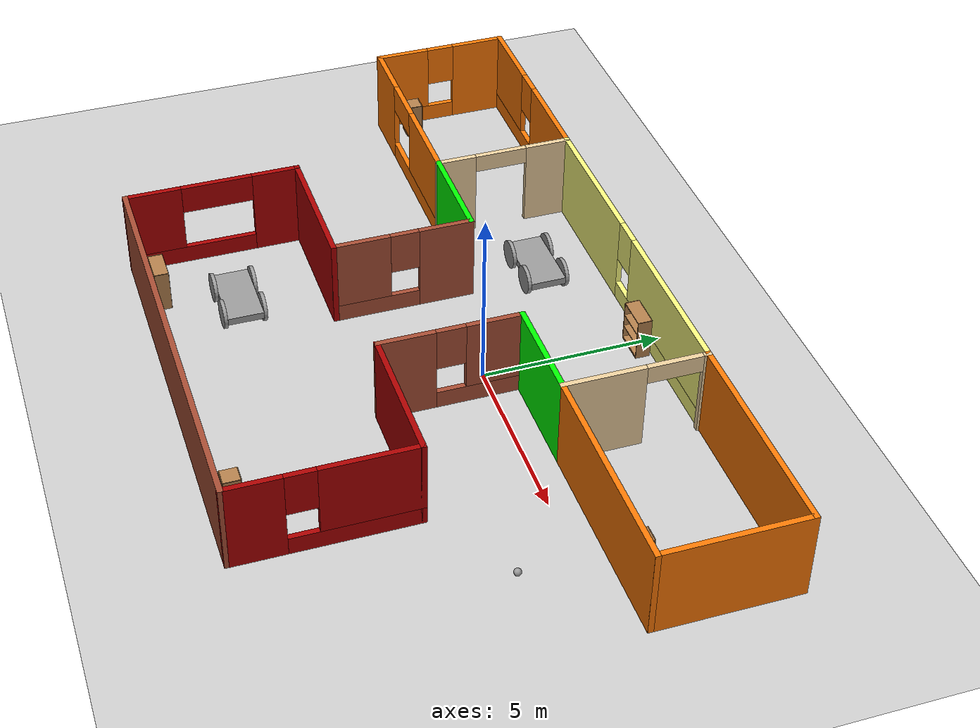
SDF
<sdf version="1.6">
 <world name="default">
  <plugin name="welcome" filename="libwelcome.so"/>
  <light name="sun" type="directional">
   <pose>0 0 10 0 -0 0</pose>
   <diffuse>0.8 0.8 0.8 1</diffuse>
   <specular>0.2 0.2 0.2 1</specular>
   <attenuation>
    <range>1000</range>
    <constant>0.9</constant>
    <linear>0.01</linear>
    <quadratic>0.001</quadratic>
   </attenuation>
   <direction>-0.5 0.1 -0.9</direction>
  </light>
  <model name="ground_plane">
   <static>1</static>
   <link name="link">
    <collision name="collision">
     <geometry><plane><normal>0 0 1</normal><size>100 100</size></plane></geometry>
     <surface><friction><ode><mu>100</mu><mu2>50</mu2></ode></friction></surface>
    </collision>
    <visual name="visual">
     <cast_shadows>0</cast_shadows>
     <geometry><plane><normal>0 0 1</normal><size>100 100</size></plane></geometry>
     <material>
      <script><uri>file://media/materials/scripts/gazebo.material</uri><name>Gazebo/Grey</name></script>
     </material>
    </visual>
   </link>
  </model>
  <gravity>0 0 -9.8</gravity>
  <magnetic_field>6e-06 2.3e-05 -4.2e-05</magnetic_field>
  <atmosphere type="adiabatic"/>
  <physics name="default_physics" default="0" type="ode">
   <max_step_size>0.001</max_step_size>
   <real_time_factor>1</real_time_factor>
   <real_time_update_rate>1000</real_time_update_rate>
  </physics>
  <scene><ambient>0.4 0.4 0.4 1</ambient><background>0.7 0.7 0.7 1</background><shadows>1</shadows></scene>
  <spherical_coordinates>
   <surface_model>EARTH_WGS84</surface_model>
   <latitude_deg>0</latitude_deg>
   <longitude_deg>0</longitude_deg>
   <elevation>0</elevation>
   <heading_deg>0</heading_deg>
  </spherical_coordinates>
  <model name="projectbuilding">
   <pose>-1.3397 -1.63448 0 0 -0 0</pose>
   <link name="Wall_0">
    <pose>0 6.2751 0 0 -0 0</pose>
    <visual name="Wall_0_Visual_0">
     <pose>-2.85668 0 1.25 0 -0 0</pose>
     <geometry><box><size>4.28664 0.15 2.5</size></box></geometry>
     <material>
      <script><uri>file://media/materials/scripts/gazebo.material</uri><name>Gazebo/Grey</name></script>
      <ambient>1 1 0.498039 1</ambient>
     </material>
     <meta><layer>0</layer></meta>
    </visual>
    <collision name="Wall_0_Collision_0">
     <geometry><box><size>4.28664 0.15 2.5</size></box></geometry>
     <pose>-2.85668 0 1.25 0 -0 0</pose>
    </collision>
    <visual name="Wall_0_Visual_1">
     <pose>2.14332 0 0.25 0 -0 0</pose>
     <geometry><box><size>5.71336 0.15 0.5</size></box></geometry>
     <material>
      <script><uri>file://media/materials/scripts/gazebo.material</uri><name>Gazebo/Grey</name></script>
      <ambient>1 1 0.498039 1</ambient>
     </material>
     <meta><layer>0</layer></meta>
    </visual>
    <collision name="Wall_0_Collision_1">
     <geometry><box><size>5.71336 0.15 0.5</size></box></geometry>
     <pose>2.14332 0 0.25 0 -0 0</pose>
    </collision>
    <visual name="Wall_0_Visual_2">
     <pose>2.54332 0 1.5 0 -0 0</pose>
     <geometry><box><size>4.91336 0.15 2</size></box></geometry>
     <material>
      <script><uri>file://media/materials/scripts/gazebo.material</uri><name>Gazebo/Grey</name></script>
      <ambient>1 1 0.498039 1</ambient>
     </material>
     <meta><layer>0</layer></meta>
    </visual>
    <collision name="Wall_0_Collision_2">
     <geometry><box><size>4.91336 0.15 2</size></box></geometry>
     <pose>2.54332 0 1.5 0 -0 0</pose>
    </collision>
    <visual name="Wall_0_Visual_3">
     <pose>-0.31336 0 1.9 0 -0 0</pose>
     <geometry><box><size>0.8 0.15 1.2</size></box></geometry>
     <material>
      <script><uri>file://media/materials/scripts/gazebo.material</uri><name>Gazebo/Grey</name></script>
      <ambient>1 1 0.498039 1</ambient>
     </material>
     <meta><layer>0</layer></meta>
    </visual>
    <collision name="Wall_0_Collision_3">
     <geometry><box><size>0.8 0.15 1.2</size></box></geometry>
     <pose>-0.31336 0 1.9 0 -0 0</pose>
    </collision>
   </link>
   <link name="Wall_16">
    <pose>-4.925 4.3501 0 0 0 -1.5708</pose>
    <visual name="Wall_16_Visual_0">
     <pose>-1.33475 0 1.25 0 -0 0</pose>
     <geometry><box><size>1.33049 0.15 2.5</size></box></geometry>
     <material>
      <script><uri>file://media/materials/scripts/gazebo.material</uri><name>Gazebo/Grey</name></script>
      <ambient>0.921569 0.807843 0.615686 1</ambient>
     </material>
     <meta><layer>0</layer></meta>
    </visual>
    <collision name="Wall_16_Collision_0">
     <geometry><box><size>1.33049 0.15 2.5</size></box></geometry>
     <pose>-1.33475 0 1.25 0 -0 0</pose>
    </collision>
    <visual name="Wall_16_Visual_1">
     <pose>1.41525 0 1.25 0 -0 0</pose>
     <geometry><box><size>1.16951 0.15 2.5</size></box></geometry>
     <material>
      <script><uri>file://media/materials/scripts/gazebo.material</uri><name>Gazebo/Grey</name></script>
      <ambient>0.921569 0.807843 0.615686 1</ambient>
     </material>
     <meta><layer>0</layer></meta>
    </visual>
    <collision name="Wall_16_Collision_1">
     <geometry><box><size>1.16951 0.15 2.5</size></box></geometry>
     <pose>1.41525 0 1.25 0 -0 0</pose>
    </collision>
    <visual name="Wall_16_Visual_2">
     <pose>0.080495 0 2.25 0 -0 0</pose>
     <geometry><box><size>1.5 0.15 0.5</size></box></geometry>
     <material>
      <script><uri>file://media/materials/scripts/gazebo.material</uri><name>Gazebo/Grey</name></script>
      <ambient>0.921569 0.807843 0.615686 1</ambient>
     </material>
     <meta><layer>0</layer></meta>
    </visual>
    <collision name="Wall_16_Collision_2">
     <geometry><box><size>1.5 0.15 0.5</size></box></geometry>
     <pose>0.080495 0 2.25 0 -0 0</pose>
    </collision>
   </link>
   <link name="Wall_17">
    <collision name="Wall_17_Collision">
     <geometry><box><size>3 0.15 2.5</size></box></geometry>
     <pose>0 0 1.25 0 -0 0</pose>
    </collision>
    <visual name="Wall_17_Visual">
     <pose>0 0 1.25 0 -0 0</pose>
     <geometry><box><size>3 0.15 2.5</size></box></geometry>
     <material>
      <script><uri>file://media/materials/scripts/gazebo.material</uri><name>Gazebo/Grey</name></script>
      <ambient>0 1 0 1</ambient>
     </material>
     <meta><layer>0</layer></meta>
    </visual>
    <pose>-3.5 2.4251 0 0 -0 0</pose>
   </link>
   <link name="Wall_19">
    <pose>4.925 4.3501 0 0 0 -1.5708</pose>
    <visual name="Wall_19_Visual_0">
     <pose>-1.89121 0 1.25 0 -0 0</pose>
     <geometry><box><size>0.217577 0.15 2.5</size></box></geometry>
     <material>
      <script><uri>file://media/materials/scripts/gazebo.material</uri><name>Gazebo/Grey</name></script>
      <ambient>0.921569 0.807843 0.615686 1</ambient>
     </material>
     <meta><layer>0</layer></meta>
    </visual>
    <collision name="Wall_19_Collision_0">
     <geometry><box><size>0.217577 0.15 2.5</size></box></geometry>
     <pose>-1.89121 0 1.25 0 -0 0</pose>
    </collision>
    <visual name="Wall_19_Visual_1">
     <pose>0.858788 0 1.25 0 -0 0</pose>
     <geometry><box><size>2.28242 0.15 2.5</size></box></geometry>
     <material>
      <script><uri>file://media/materials/scripts/gazebo.material</uri><name>Gazebo/Grey</name></script>
      <ambient>0.921569 0.807843 0.615686 1</ambient>
     </material>
     <meta><layer>0</layer></meta>
    </visual>
    <collision name="Wall_19_Collision_1">
     <geometry><box><size>2.28242 0.15 2.5</size></box></geometry>
     <pose>0.858788 0 1.25 0 -0 0</pose>
    </collision>
    <visual name="Wall_19_Visual_2">
     <pose>-1.03242 0 2.25 0 -0 0</pose>
     <geometry><box><size>1.5 0.15 0.5</size></box></geometry>
     <material>
      <script><uri>file://media/materials/scripts/gazebo.material</uri><name>Gazebo/Grey</name></script>
      <ambient>0.921569 0.807843 0.615686 1</ambient>
     </material>
     <meta><layer>0</layer></meta>
    </visual>
    <collision name="Wall_19_Collision_2">
     <geometry><box><size>1.5 0.15 0.5</size></box></geometry>
     <pose>-1.03242 0 2.25 0 -0 0</pose>
    </collision>
   </link>
   <link name="Wall_20">
    <collision name="Wall_20_Collision">
     <geometry><box><size>3 0.15 2.5</size></box></geometry>
     <pose>0 0 1.25 0 -0 0</pose>
    </collision>
    <visual name="Wall_20_Visual">
     <pose>0 0 1.25 0 -0 0</pose>
     <geometry><box><size>3 0.15 2.5</size></box></geometry>
     <material>
      <script><uri>file://media/materials/scripts/gazebo.material</uri><name>Gazebo/Grey</name></script>
      <ambient>0 1 0 1</ambient>
     </material>
     <meta><layer>0</layer></meta>
    </visual>
    <pose>3.5 2.4251 0 0 -0 3.14159</pose>
   </link>
   <link name="Wall_44">
    <pose>-2.075 0.5001 0 0 0 -1.5708</pose>
    <visual name="Wall_44_Visual_0">
     <pose>-1.22523 0 1.25 0 -0 0</pose>
     <geometry><box><size>1.54953 0.15 2.5</size></box></geometry>
     <material>
      <script><uri>file://media/materials/scripts/gazebo.material</uri><name>Gazebo/Bricks</name></script>
      <ambient>0 0.333333 0 1</ambient>
     </material>
     <meta><layer>0</layer></meta>
    </visual>
    <collision name="Wall_44_Collision_0">
     <geometry><box><size>1.54953 0.15 2.5</size></box></geometry>
     <pose>-1.22523 0 1.25 0 -0 0</pose>
    </collision>
    <visual name="Wall_44_Visual_1">
     <pose>0.774766 0 0.25 0 -0 0</pose>
     <geometry><box><size>2.45047 0.15 0.5</size></box></geometry>
     <material>
      <script><uri>file://media/materials/scripts/gazebo.material</uri><name>Gazebo/Bricks</name></script>
      <ambient>0 0.333333 0 1</ambient>
     </material>
     <meta><layer>0</layer></meta>
    </visual>
    <collision name="Wall_44_Collision_1">
     <geometry><box><size>2.45047 0.15 0.5</size></box></geometry>
     <pose>0.774766 0 0.25 0 -0 0</pose>
    </collision>
    <visual name="Wall_44_Visual_2">
     <pose>1.17477 0 1.5 0 -0 0</pose>
     <geometry><box><size>1.65047 0.15 2</size></box></geometry>
     <material>
      <script><uri>file://media/materials/scripts/gazebo.material</uri><name>Gazebo/Bricks</name></script>
      <ambient>0 0.333333 0 1</ambient>
     </material>
     <meta><layer>0</layer></meta>
    </visual>
    <collision name="Wall_44_Collision_2">
     <geometry><box><size>1.65047 0.15 2</size></box></geometry>
     <pose>1.17477 0 1.5 0 -0 0</pose>
    </collision>
    <visual name="Wall_44_Visual_3">
     <pose>-0.050468 0 1.9 0 -0 0</pose>
     <geometry><box><size>0.8 0.15 1.2</size></box></geometry>
     <material>
      <script><uri>file://media/materials/scripts/gazebo.material</uri><name>Gazebo/Bricks</name></script>
      <ambient>0 0.333333 0 1</ambient>
     </material>
     <meta><layer>0</layer></meta>
    </visual>
    <collision name="Wall_44_Collision_3">
     <geometry><box><size>0.8 0.15 1.2</size></box></geometry>
     <pose>-0.050468 0 1.9 0 -0 0</pose>
    </collision>
   </link>
   <link name="Wall_45">
    <collision name="Wall_45_Collision">
     <geometry><box><size>4 0.15 2.5</size></box></geometry>
     <pose>0 0 1.25 0 -0 0</pose>
    </collision>
    <visual name="Wall_45_Visual">
     <pose>0 0 1.25 0 -0 0</pose>
     <geometry><box><size>4 0.15 2.5</size></box></geometry>
     <material>
      <script><uri>file://media/materials/scripts/gazebo.material</uri><name>Gazebo/Grey</name></script>
      <ambient>0.666667 0 0 1</ambient>
     </material>
     <meta><layer>0</layer></meta>
    </visual>
    <pose>-4 -1.4249 0 0 -0 3.14159</pose>
   </link>
   <link name="Wall_46">
    <pose>-5.925 -3.8499 0 0 0 -1.5708</pose>
    <visual name="Wall_46_Visual_0">
     <pose>-1.81013 0 1.25 0 -0 0</pose>
     <geometry><box><size>1.37973 0.15 2.5</size></box></geometry>
     <material>
      <script><uri>file://media/materials/scripts/gazebo.material</uri><name>Gazebo/Grey</name></script>
      <ambient>0.666667 0 0 1</ambient>
     </material>
     <meta><layer>0</layer></meta>
    </visual>
    <collision name="Wall_46_Collision_0">
     <geometry><box><size>1.37973 0.15 2.5</size></box></geometry>
     <pose>-1.81013 0 1.25 0 -0 0</pose>
    </collision>
    <visual name="Wall_46_Visual_1">
     <pose>0.689866 0 0.25 0 -0 0</pose>
     <geometry><box><size>3.62027 0.15 0.5</size></box></geometry>
     <material>
      <script><uri>file://media/materials/scripts/gazebo.material</uri><name>Gazebo/Grey</name></script>
      <ambient>0.666667 0 0 1</ambient>
     </material>
     <meta><layer>0</layer></meta>
    </visual>
    <collision name="Wall_46_Collision_1">
     <geometry><box><size>3.62027 0.15 0.5</size></box></geometry>
     <pose>0.689866 0 0.25 0 -0 0</pose>
    </collision>
    <visual name="Wall_46_Visual_2">
     <pose>1.68987 0 1.5 0 -0 0</pose>
     <geometry><box><size>1.62027 0.15 2</size></box></geometry>
     <material>
      <script><uri>file://media/materials/scripts/gazebo.material</uri><name>Gazebo/Grey</name></script>
      <ambient>0.666667 0 0 1</ambient>
     </material>
     <meta><layer>0</layer></meta>
    </visual>
    <collision name="Wall_46_Collision_2">
     <geometry><box><size>1.62027 0.15 2</size></box></geometry>
     <pose>1.68987 0 1.5 0 -0 0</pose>
    </collision>
    <visual name="Wall_46_Visual_3">
     <pose>-0.120268 0 2.1 0 -0 0</pose>
     <geometry><box><size>2 0.15 0.8</size></box></geometry>
     <material>
      <script><uri>file://media/materials/scripts/gazebo.material</uri><name>Gazebo/Grey</name></script>
      <ambient>0.666667 0 0 1</ambient>
     </material>
     <meta><layer>0</layer></meta>
    </visual>
    <collision name="Wall_46_Collision_3">
     <geometry><box><size>2 0.15 0.8</size></box></geometry>
     <pose>-0.120268 0 2.1 0 -0 0</pose>
    </collision>
   </link>
   <link name="Wall_52">
    <collision name="Wall_52_Collision">
     <geometry><box><size>12 0.15 2.5</size></box></geometry>
     <pose>0 0 1.25 0 -0 0</pose>
    </collision>
    <visual name="Wall_52_Visual">
     <pose>0 0 1.25 0 -0 0</pose>
     <geometry><box><size>12 0.15 2.5</size></box></geometry>
     <material>
      <script><uri>file://media/materials/scripts/gazebo.material</uri><name>Gazebo/Bricks</name></script>
      <ambient>0.666667 0 0 1</ambient>
     </material>
     <meta><layer>0</layer></meta>
    </visual>
    <pose>0 -6.2749 0 0 -0 0</pose>
   </link>
   <link name="Wall_54">
    <pose>5.92523 -3.85009 0 0 -0 1.5707</pose>
    <visual name="Wall_54_Visual_0">
     <pose>-1.72268 0 1.25 0 -0 0</pose>
     <geometry><box><size>1.55464 0.15 2.5</size></box></geometry>
     <material>
      <script><uri>file://media/materials/scripts/gazebo.material</uri><name>Gazebo/Grey</name></script>
      <ambient>0.666667 0 0 1</ambient>
     </material>
     <meta><layer>0</layer></meta>
    </visual>
    <collision name="Wall_54_Collision_0">
     <geometry><box><size>1.55464 0.15 2.5</size></box></geometry>
     <pose>-1.72268 0 1.25 0 -0 0</pose>
    </collision>
    <visual name="Wall_54_Visual_1">
     <pose>0.777321 0 0.25 0 -0 0</pose>
     <geometry><box><size>3.44536 0.15 0.5</size></box></geometry>
     <material>
      <script><uri>file://media/materials/scripts/gazebo.material</uri><name>Gazebo/Grey</name></script>
      <ambient>0.666667 0 0 1</ambient>
     </material>
     <meta><layer>0</layer></meta>
    </visual>
    <collision name="Wall_54_Collision_1">
     <geometry><box><size>3.44536 0.15 0.5</size></box></geometry>
     <pose>0.777321 0 0.25 0 -0 0</pose>
    </collision>
    <visual name="Wall_54_Visual_2">
     <pose>1.17732 0 1.5 0 -0 0</pose>
     <geometry><box><size>2.64536 0.15 2</size></box></geometry>
     <material>
      <script><uri>file://media/materials/scripts/gazebo.material</uri><name>Gazebo/Grey</name></script>
      <ambient>0.666667 0 0 1</ambient>
     </material>
     <meta><layer>0</layer></meta>
    </visual>
    <collision name="Wall_54_Collision_2">
     <geometry><box><size>2.64536 0.15 2</size></box></geometry>
     <pose>1.17732 0 1.5 0 -0 0</pose>
    </collision>
    <visual name="Wall_54_Visual_3">
     <pose>-0.545359 0 1.9 0 -0 0</pose>
     <geometry><box><size>0.8 0.15 1.2</size></box></geometry>
     <material>
      <script><uri>file://media/materials/scripts/gazebo.material</uri><name>Gazebo/Grey</name></script>
      <ambient>0.666667 0 0 1</ambient>
     </material>
     <meta><layer>0</layer></meta>
    </visual>
    <collision name="Wall_54_Collision_3">
     <geometry><box><size>0.8 0.15 1.2</size></box></geometry>
     <pose>-0.545359 0 1.9 0 -0 0</pose>
    </collision>
   </link>
   <link name="Wall_56">
    <collision name="Wall_56_Collision">
     <geometry><box><size>4 0.15 2.5</size></box></geometry>
     <pose>0 0 1.25 0 -0 0</pose>
    </collision>
    <visual name="Wall_56_Visual">
     <pose>0 0 1.25 0 -0 0</pose>
     <geometry><box><size>4 0.15 2.5</size></box></geometry>
     <material>
      <script><uri>file://media/materials/scripts/gazebo.material</uri><name>Gazebo/Grey</name></script>
      <ambient>0.666667 0 0 1</ambient>
     </material>
     <meta><layer>0</layer></meta>
    </visual>
    <pose>4.00046 -1.42529 0 0 -0 3.14159</pose>
   </link>
   <link name="Wall_58">
    <pose>2.07523 0.499906 0 0 -0 1.57092</pose>
    <visual name="Wall_58_Visual_0">
     <pose>-1.19803 0 1.25 0 -0 0</pose>
     <geometry><box><size>1.60433 0.15 2.5</size></box></geometry>
     <material>
      <script><uri>file://media/materials/scripts/gazebo.material</uri><name>Gazebo/Bricks</name></script>
      <ambient>0 0.333333 0 1</ambient>
     </material>
     <meta><layer>0</layer></meta>
    </visual>
    <collision name="Wall_58_Collision_0">
     <geometry><box><size>1.60433 0.15 2.5</size></box></geometry>
     <pose>-1.19803 0 1.25 0 -0 0</pose>
    </collision>
    <visual name="Wall_58_Visual_1">
     <pose>0.802167 0 0.25 0 -0 0</pose>
     <geometry><box><size>2.39606 0.15 0.5</size></box></geometry>
     <material>
      <script><uri>file://media/materials/scripts/gazebo.material</uri><name>Gazebo/Bricks</name></script>
      <ambient>0 0.333333 0 1</ambient>
     </material>
     <meta><layer>0</layer></meta>
    </visual>
    <collision name="Wall_58_Collision_1">
     <geometry><box><size>2.39606 0.15 0.5</size></box></geometry>
     <pose>0.802167 0 0.25 0 -0 0</pose>
    </collision>
    <visual name="Wall_58_Visual_2">
     <pose>1.20217 0 1.5 0 -0 0</pose>
     <geometry><box><size>1.59606 0.15 2</size></box></geometry>
     <material>
      <script><uri>file://media/materials/scripts/gazebo.material</uri><name>Gazebo/Bricks</name></script>
      <ambient>0 0.333333 0 1</ambient>
     </material>
     <meta><layer>0</layer></meta>
    </visual>
    <collision name="Wall_58_Collision_2">
     <geometry><box><size>1.59606 0.15 2</size></box></geometry>
     <pose>1.20217 0 1.5 0 -0 0</pose>
    </collision>
    <visual name="Wall_58_Visual_3">
     <pose>0.004139 0 1.9 0 -0 0</pose>
     <geometry><box><size>0.8 0.15 1.2</size></box></geometry>
     <material>
      <script><uri>file://media/materials/scripts/gazebo.material</uri><name>Gazebo/Bricks</name></script>
      <ambient>0 0.333333 0 1</ambient>
     </material>
     <meta><layer>0</layer></meta>
    </visual>
    <collision name="Wall_58_Collision_3">
     <geometry><box><size>0.8 0.15 1.2</size></box></geometry>
     <pose>0.004139 0 1.9 0 -0 0</pose>
    </collision>
   </link>
   <link name="Wall_60">
    <collision name="Wall_60_Collision">
     <geometry><box><size>6 0.15 2.5</size></box></geometry>
     <pose>0 0 1.25 0 -0 0</pose>
    </collision>
    <visual name="Wall_60_Visual">
     <pose>0 0 1.25 0 -0 0</pose>
     <geometry><box><size>6 0.15 2.5</size></box></geometry>
     <material>
      <script><uri>file://media/materials/scripts/gazebo.material</uri><name>Gazebo/Grey</name></script>
      <ambient>0.996078 0.47451 0.0196078 1</ambient>
     </material>
     <meta><layer>0</layer></meta>
    </visual>
    <pose>7.85 6.2751 0 0 -0 0</pose>
   </link>
   <link name="Wall_62">
    <collision name="Wall_62_Collision">
     <geometry><box><size>4 0.15 2.5</size></box></geometry>
     <pose>0 0 1.25 0 -0 0</pose>
    </collision>
    <visual name="Wall_62_Visual">
     <pose>0 0 1.25 0 -0 0</pose>
     <geometry><box><size>4 0.15 2.5</size></box></geometry>
     <material>
      <script><uri>file://media/materials/scripts/gazebo.material</uri><name>Gazebo/Grey</name></script>
      <ambient>0.996078 0.47451 0.0196078 1</ambient>
     </material>
     <meta><layer>0</layer></meta>
    </visual>
    <pose>10.775 4.3501 0 0 0 -1.5708</pose>
   </link>
   <link name="Wall_64">
    <collision name="Wall_64_Collision">
     <geometry><box><size>6 0.15 2.5</size></box></geometry>
     <pose>0 0 1.25 0 -0 0</pose>
    </collision>
    <visual name="Wall_64_Visual">
     <pose>0 0 1.25 0 -0 0</pose>
     <geometry><box><size>6 0.15 2.5</size></box></geometry>
     <material>
      <script><uri>file://media/materials/scripts/gazebo.material</uri><name>Gazebo/Grey</name></script>
      <ambient>0.996078 0.47451 0.0196078 1</ambient>
     </material>
     <meta><layer>0</layer></meta>
    </visual>
    <pose>7.85 2.4251 0 0 -0 0</pose>
   </link>
   <link name="Wall_66">
    <pose>-7.85 6.2751 0 0 -0 3.14159</pose>
    <visual name="Wall_66_Visual_0">
     <pose>-1.57139 0 1.25 0 -0 0</pose>
     <geometry><box><size>2.85722 0.15 2.5</size></box></geometry>
     <material>
      <script><uri>file://media/materials/scripts/gazebo.material</uri><name>Gazebo/Grey</name></script>
      <ambient>0.996078 0.47451 0.0196078 1</ambient>
     </material>
     <meta><layer>0</layer></meta>
    </visual>
    <collision name="Wall_66_Collision_0">
     <geometry><box><size>2.85722 0.15 2.5</size></box></geometry>
     <pose>-1.57139 0 1.25 0 -0 0</pose>
    </collision>
    <visual name="Wall_66_Visual_1">
     <pose>1.42861 0 0.25 0 -0 0</pose>
     <geometry><box><size>3.14278 0.15 0.5</size></box></geometry>
     <material>
      <script><uri>file://media/materials/scripts/gazebo.material</uri><name>Gazebo/Grey</name></script>
      <ambient>0.996078 0.47451 0.0196078 1</ambient>
     </material>
     <meta><layer>0</layer></meta>
    </visual>
    <collision name="Wall_66_Collision_1">
     <geometry><box><size>3.14278 0.15 0.5</size></box></geometry>
     <pose>1.42861 0 0.25 0 -0 0</pose>
    </collision>
    <visual name="Wall_66_Visual_2">
     <pose>1.82861 0 1.5 0 -0 0</pose>
     <geometry><box><size>2.34278 0.15 2</size></box></geometry>
     <material>
      <script><uri>file://media/materials/scripts/gazebo.material</uri><name>Gazebo/Grey</name></script>
      <ambient>0.996078 0.47451 0.0196078 1</ambient>
     </material>
     <meta><layer>0</layer></meta>
    </visual>
    <collision name="Wall_66_Collision_2">
     <geometry><box><size>2.34278 0.15 2</size></box></geometry>
     <pose>1.82861 0 1.5 0 -0 0</pose>
    </collision>
    <visual name="Wall_66_Visual_3">
     <pose>0.257217 0 1.9 0 -0 0</pose>
     <geometry><box><size>0.8 0.15 1.2</size></box></geometry>
     <material>
      <script><uri>file://media/materials/scripts/gazebo.material</uri><name>Gazebo/Grey</name></script>
      <ambient>0.996078 0.47451 0.0196078 1</ambient>
     </material>
     <meta><layer>0</layer></meta>
    </visual>
    <collision name="Wall_66_Collision_3">
     <geometry><box><size>0.8 0.15 1.2</size></box></geometry>
     <pose>0.257217 0 1.9 0 -0 0</pose>
    </collision>
   </link>
   <link name="Wall_68">
    <pose>-10.775 4.3501 0 0 0 -1.5708</pose>
    <visual name="Wall_68_Visual_0">
     <pose>-1.1893 0 1.25 0 -0 0</pose>
     <geometry><box><size>1.62141 0.15 2.5</size></box></geometry>
     <material>
      <script><uri>file://media/materials/scripts/gazebo.material</uri><name>Gazebo/Grey</name></script>
      <ambient>0.996078 0.47451 0.0196078 1</ambient>
     </material>
     <meta><layer>0</layer></meta>
    </visual>
    <collision name="Wall_68_Collision_0">
     <geometry><box><size>1.62141 0.15 2.5</size></box></geometry>
     <pose>-1.1893 0 1.25 0 -0 0</pose>
    </collision>
    <visual name="Wall_68_Visual_1">
     <pose>0.810704 0 0.25 0 -0 0</pose>
     <geometry><box><size>2.37859 0.15 0.5</size></box></geometry>
     <material>
      <script><uri>file://media/materials/scripts/gazebo.material</uri><name>Gazebo/Grey</name></script>
      <ambient>0.996078 0.47451 0.0196078 1</ambient>
     </material>
     <meta><layer>0</layer></meta>
    </visual>
    <collision name="Wall_68_Collision_1">
     <geometry><box><size>2.37859 0.15 0.5</size></box></geometry>
     <pose>0.810704 0 0.25 0 -0 0</pose>
    </collision>
    <visual name="Wall_68_Visual_2">
     <pose>1.2107 0 1.5 0 -0 0</pose>
     <geometry><box><size>1.57859 0.15 2</size></box></geometry>
     <material>
      <script><uri>file://media/materials/scripts/gazebo.material</uri><name>Gazebo/Grey</name></script>
      <ambient>0.996078 0.47451 0.0196078 1</ambient>
     </material>
     <meta><layer>0</layer></meta>
    </visual>
    <collision name="Wall_68_Collision_2">
     <geometry><box><size>1.57859 0.15 2</size></box></geometry>
     <pose>1.2107 0 1.5 0 -0 0</pose>
    </collision>
    <visual name="Wall_68_Visual_3">
     <pose>0.021408 0 1.9 0 -0 0</pose>
     <geometry><box><size>0.8 0.15 1.2</size></box></geometry>
     <material>
      <script><uri>file://media/materials/scripts/gazebo.material</uri><name>Gazebo/Grey</name></script>
      <ambient>0.996078 0.47451 0.0196078 1</ambient>
     </material>
     <meta><layer>0</layer></meta>
    </visual>
    <collision name="Wall_68_Collision_3">
     <geometry><box><size>0.8 0.15 1.2</size></box></geometry>
     <pose>0.021408 0 1.9 0 -0 0</pose>
    </collision>
   </link>
   <link name="Wall_70">
    <pose>-7.85 2.4251 0 0 -0 0</pose>
    <visual name="Wall_70_Visual_0">
     <pose>-2.09671 0 1.25 0 -0 0</pose>
     <geometry><box><size>1.80658 0.15 2.5</size></box></geometry>
     <material>
      <script><uri>file://media/materials/scripts/gazebo.material</uri><name>Gazebo/Grey</name></script>
      <ambient>0.996078 0.47451 0.0196078 1</ambient>
     </material>
     <meta><layer>0</layer></meta>
    </visual>
    <collision name="Wall_70_Collision_0">
     <geometry><box><size>1.80658 0.15 2.5</size></box></geometry>
     <pose>-2.09671 0 1.25 0 -0 0</pose>
    </collision>
    <visual name="Wall_70_Visual_1">
     <pose>0.903291 0 0.25 0 -0 0</pose>
     <geometry><box><size>4.19342 0.15 0.5</size></box></geometry>
     <material>
      <script><uri>file://media/materials/scripts/gazebo.material</uri><name>Gazebo/Grey</name></script>
      <ambient>0.996078 0.47451 0.0196078 1</ambient>
     </material>
     <meta><layer>0</layer></meta>
    </visual>
    <collision name="Wall_70_Collision_1">
     <geometry><box><size>4.19342 0.15 0.5</size></box></geometry>
     <pose>0.903291 0 0.25 0 -0 0</pose>
    </collision>
    <visual name="Wall_70_Visual_2">
     <pose>1.65329 0 1.5 0 -0 0</pose>
     <geometry><box><size>2.69342 0.15 2</size></box></geometry>
     <material>
      <script><uri>file://media/materials/scripts/gazebo.material</uri><name>Gazebo/Grey</name></script>
      <ambient>0.996078 0.47451 0.0196078 1</ambient>
     </material>
     <meta><layer>0</layer></meta>
    </visual>
    <collision name="Wall_70_Collision_2">
     <geometry><box><size>2.69342 0.15 2</size></box></geometry>
     <pose>1.65329 0 1.5 0 -0 0</pose>
    </collision>
    <visual name="Wall_70_Visual_3">
     <pose>-0.443419 0 2.1 0 -0 0</pose>
     <geometry><box><size>1.5 0.15 0.8</size></box></geometry>
     <material>
      <script><uri>file://media/materials/scripts/gazebo.material</uri><name>Gazebo/Grey</name></script>
      <ambient>0.996078 0.47451 0.0196078 1</ambient>
     </material>
     <meta><layer>0</layer></meta>
    </visual>
    <collision name="Wall_70_Collision_3">
     <geometry><box><size>1.5 0.15 0.8</size></box></geometry>
     <pose>-0.443419 0 2.1 0 -0 0</pose>
    </collision>
   </link>
   <static>1</static>
  </model>
  <model name="projectmodel">
   <link name="link_0">
    <pose>0.001777 0 0 0 -0 0</pose>
    <inertial>
     <mass>1</mass>
     <inertia>
      <ixx>0.166667</ixx>
      <ixy>0</ixy>
      <ixz>0</ixz>
      <iyy>0.166667</iyy>
      <iyz>0</iyz>
      <izz>0.166667</izz>
     </inertia>
    </inertial>
    <visual name="visual">
     <geometry><box><size>2 1 0.2</size></box></geometry>
     <material>
      <lighting>1</lighting>
      <script><uri>file://media/materials/scripts/gazebo.material</uri><name>Gazebo/Grey</name></script>
      <shader type="pixel"><normal_map>__default__</normal_map></shader>
      <ambient>0.3 0.3 0.3 1</ambient>
      <diffuse>0.7 0.7 0.7 1</diffuse>
      <specular>0.01 0.01 0.01 1</specular>
      <emissive>0 0 0 1</emissive>
     </material>
    </visual>
    <collision name="collision">
     <geometry><box><size>2 1 0.2</size></box></geometry>
     <surface>
      <friction>
       <ode><mu>1</mu><mu2>1</mu2><fdir1>0 0 0</fdir1><slip1>0</slip1><slip2>0</slip2></ode>
       <torsional>
        <coefficient>1</coefficient>
        <patch_radius>0</patch_radius>
        <surface_radius>0</surface_radius>
        <use_patch_radius>1</use_patch_radius>
        <ode><slip>0</slip></ode>
       </torsional>
      </friction>
      <bounce><restitution_coefficient>0</restitution_coefficient><threshold>1e+06</threshold></bounce>
      <contact>
       <collide_without_contact>0</collide_without_contact>
       <collide_without_contact_bitmask>1</collide_without_contact_bitmask>
       <collide_bitmask>1</collide_bitmask>
       <ode>
        <soft_cfm>0</soft_cfm>
        <soft_erp>0.2</soft_erp>
        <kp>1e+13</kp>
        <kd>1</kd>
        <max_vel>0.01</max_vel>
        <min_depth>0</min_depth>
       </ode>
       <bullet>
        <split_impulse>1</split_impulse>
        <split_impulse_penetration_threshold>-0.01</split_impulse_penetration_threshold>
        <soft_cfm>0</soft_cfm>
        <soft_erp>0.2</soft_erp>
        <kp>1e+13</kp>
        <kd>1</kd>
       </bullet>
      </contact>
     </surface>
    </collision>
   </link>
   <link name="link_1">
    <pose>0.601777 -0.550039 0 1.5707 -0 0</pose>
    <inertial>
     <mass>1</mass>
     <inertia><ixx>0.145833</ixx><ixy>0</ixy><ixz>0</ixz><iyy>0.145833</iyy><iyz>0</iyz><izz>0.125</izz></inertia>
    </inertial>
    <visual name="visual">
     <geometry><cylinder><radius>0.4</radius><length>0.1</length></cylinder></geometry>
     <material>
      <lighting>1</lighting>
      <script><uri>file://media/materials/scripts/gazebo.material</uri><name>Gazebo/Grey</name></script>
      <shader type="pixel"><normal_map>__default__</normal_map></shader>
      <ambient>0.3 0.3 0.3 1</ambient>
      <diffuse>0.7 0.7 0.7 1</diffuse>
      <specular>0.01 0.01 0.01 1</specular>
      <emissive>0 0 0 1</emissive>
     </material>
    </visual>
    <collision name="collision">
     <geometry><cylinder><radius>0.4</radius><length>0.1</length></cylinder></geometry>
     <surface>
      <friction>
       <ode><mu>1</mu><mu2>1</mu2><fdir1>0 0 0</fdir1><slip1>0</slip1><slip2>0</slip2></ode>
       <torsional>
        <coefficient>1</coefficient>
        <patch_radius>0</patch_radius>
        <surface_radius>0</surface_radius>
        <use_patch_radius>1</use_patch_radius>
        <ode><slip>0</slip></ode>
       </torsional>
      </friction>
      <bounce><restitution_coefficient>0</restitution_coefficient><threshold>1e+06</threshold></bounce>
      <contact>
       <collide_without_contact>0</collide_without_contact>
       <collide_without_contact_bitmask>1</collide_without_contact_bitmask>
       <collide_bitmask>1</collide_bitmask>
       <ode>
        <soft_cfm>0</soft_cfm>
        <soft_erp>0.2</soft_erp>
        <kp>1e+13</kp>
        <kd>1</kd>
        <max_vel>0.01</max_vel>
        <min_depth>0</min_depth>
       </ode>
       <bullet>
        <split_impulse>1</split_impulse>
        <split_impulse_penetration_threshold>-0.01</split_impulse_penetration_threshold>
        <soft_cfm>0</soft_cfm>
        <soft_erp>0.2</soft_erp>
        <kp>1e+13</kp>
        <kd>1</kd>
       </bullet>
      </contact>
     </surface>
    </collision>
   </link>
   <link name="link_1_clone">
    <pose>0.601777 0.550039 0 1.5707 -0 0</pose>
    <inertial>
     <mass>1</mass>
     <inertia><ixx>0.145833</ixx><ixy>0</ixy><ixz>0</ixz><iyy>0.145833</iyy><iyz>0</iyz><izz>0.125</izz></inertia>
    </inertial>
    <visual name="visual">
     <geometry><cylinder><radius>0.4</radius><length>0.1</length></cylinder></geometry>
     <material>
      <lighting>1</lighting>
      <script><uri>file://media/materials/scripts/gazebo.material</uri><name>Gazebo/Grey</name></script>
      <shader type="pixel"><normal_map>__default__</normal_map></shader>
      <ambient>0.3 0.3 0.3 1</ambient>
      <diffuse>0.7 0.7 0.7 1</diffuse>
      <specular>0.01 0.01 0.01 1</specular>
      <emissive>0 0 0 1</emissive>
     </material>
    </visual>
    <collision name="collision">
     <geometry><cylinder><radius>0.4</radius><length>0.1</length></cylinder></geometry>
     <surface>
      <friction>
       <ode><mu>1</mu><mu2>1</mu2><fdir1>0 0 0</fdir1><slip1>0</slip1><slip2>0</slip2></ode>
       <torsional>
        <coefficient>1</coefficient>
        <patch_radius>0</patch_radius>
        <surface_radius>0</surface_radius>
        <use_patch_radius>1</use_patch_radius>
        <ode><slip>0</slip></ode>
       </torsional>
      </friction>
      <bounce><restitution_coefficient>0</restitution_coefficient><threshold>1e+06</threshold></bounce>
      <contact>
       <collide_without_contact>0</collide_without_contact>
       <collide_without_contact_bitmask>1</collide_without_contact_bitmask>
       <collide_bitmask>1</collide_bitmask>
       <ode>
        <soft_cfm>0</soft_cfm>
        <soft_erp>0.2</soft_erp>
        <kp>1e+13</kp>
        <kd>1</kd>
        <max_vel>0.01</max_vel>
        <min_depth>0</min_depth>
       </ode>
       <bullet>
        <split_impulse>1</split_impulse>
        <split_impulse_penetration_threshold>-0.01</split_impulse_penetration_threshold>
        <soft_cfm>0</soft_cfm>
        <soft_erp>0.2</soft_erp>
        <kp>1e+13</kp>
        <kd>1</kd>
       </bullet>
      </contact>
     </surface>
    </collision>
   </link>
   <link name="link_1_clone_0">
    <pose>-0.607108 0.550039 0 1.5707 -0 0</pose>
    <inertial>
     <mass>1</mass>
     <inertia><ixx>0.145833</ixx><ixy>0</ixy><ixz>0</ixz><iyy>0.145833</iyy><iyz>0</iyz><izz>0.125</izz></inertia>
    </inertial>
    <visual name="visual">
     <geometry><cylinder><radius>0.4</radius><length>0.1</length></cylinder></geometry>
     <material>
      <lighting>1</lighting>
      <script><uri>file://media/materials/scripts/gazebo.material</uri><name>Gazebo/Grey</name></script>
      <shader type="pixel"><normal_map>__default__</normal_map></shader>
      <ambient>0.3 0.3 0.3 1</ambient>
      <diffuse>0.7 0.7 0.7 1</diffuse>
      <specular>0.01 0.01 0.01 1</specular>
      <emissive>0 0 0 1</emissive>
     </material>
    </visual>
    <collision name="collision">
     <geometry><cylinder><radius>0.4</radius><length>0.1</length></cylinder></geometry>
     <surface>
      <friction>
       <ode><mu>1</mu><mu2>1</mu2><fdir1>0 0 0</fdir1><slip1>0</slip1><slip2>0</slip2></ode>
       <torsional>
        <coefficient>1</coefficient>
        <patch_radius>0</patch_radius>
        <surface_radius>0</surface_radius>
        <use_patch_radius>1</use_patch_radius>
        <ode><slip>0</slip></ode>
       </torsional>
      </friction>
      <bounce><restitution_coefficient>0</restitution_coefficient><threshold>1e+06</threshold></bounce>
      <contact>
       <collide_without_contact>0</collide_without_contact>
       <collide_without_contact_bitmask>1</collide_without_contact_bitmask>
       <collide_bitmask>1</collide_bitmask>
       <ode>
        <soft_cfm>0</soft_cfm>
        <soft_erp>0.2</soft_erp>
        <kp>1e+13</kp>
        <kd>1</kd>
        <max_vel>0.01</max_vel>
        <min_depth>0</min_depth>
       </ode>
       <bullet>
        <split_impulse>1</split_impulse>
        <split_impulse_penetration_threshold>-0.01</split_impulse_penetration_threshold>
        <soft_cfm>0</soft_cfm>
        <soft_erp>0.2</soft_erp>
        <kp>1e+13</kp>
        <kd>1</kd>
       </bullet>
      </contact>
     </surface>
    </collision>
   </link>
   <link name="link_1_clone_0_clone">
    <pose>-0.598223 -0.550039 0 1.5707 -0 0</pose>
    <inertial>
     <mass>1</mass>
     <inertia><ixx>0.145833</ixx><ixy>0</ixy><ixz>0</ixz><iyy>0.145833</iyy><iyz>0</iyz><izz>0.125</izz></inertia>
    </inertial>
    <visual name="visual">
     <geometry><cylinder><radius>0.4</radius><length>0.1</length></cylinder></geometry>
     <material>
      <lighting>1</lighting>
      <script><uri>file://media/materials/scripts/gazebo.material</uri><name>Gazebo/Grey</name></script>
      <shader type="pixel"><normal_map>__default__</normal_map></shader>
      <ambient>0.3 0.3 0.3 1</ambient>
      <diffuse>0.7 0.7 0.7 1</diffuse>
      <specular>0.01 0.01 0.01 1</specular>
      <emissive>0 0 0 1</emissive>
     </material>
    </visual>
    <collision name="collision">
     <geometry><cylinder><radius>0.4</radius><length>0.1</length></cylinder></geometry>
     <surface>
      <friction>
       <ode><mu>1</mu><mu2>1</mu2><fdir1>0 0 0</fdir1><slip1>0</slip1><slip2>0</slip2></ode>
       <torsional>
        <coefficient>1</coefficient>
        <patch_radius>0</patch_radius>
        <surface_radius>0</surface_radius>
        <use_patch_radius>1</use_patch_radius>
        <ode><slip>0</slip></ode>
       </torsional>
      </friction>
      <bounce><restitution_coefficient>0</restitution_coefficient><threshold>1e+06</threshold></bounce>
      <contact>
       <collide_without_contact>0</collide_without_contact>
       <collide_without_contact_bitmask>1</collide_without_contact_bitmask>
       <collide_bitmask>1</collide_bitmask>
       <ode>
        <soft_cfm>0</soft_cfm>
        <soft_erp>0.2</soft_erp>
        <kp>1e+13</kp>
        <kd>1</kd>
        <max_vel>0.01</max_vel>
        <min_depth>0</min_depth>
       </ode>
       <bullet>
        <split_impulse>1</split_impulse>
        <split_impulse_penetration_threshold>-0.01</split_impulse_penetration_threshold>
        <soft_cfm>0</soft_cfm>
        <soft_erp>0.2</soft_erp>
        <kp>1e+13</kp>
        <kd>1</kd>
       </bullet>
      </contact>
     </surface>
    </collision>
   </link>
   <joint name="link_0_JOINT_0" type="revolute">
    <parent>link_0</parent>
    <child>link_1</child>
    <axis>
     <xyz>0 0 1</xyz>
     <use_parent_model_frame>0</use_parent_model_frame>
     <limit>
      <lower>-1.79769e+308</lower>
      <upper>1.79769e+308</upper>
      <effort>-1</effort>
      <velocity>-1</velocity>
     </limit>
     <dynamics>
      <spring_reference>0</spring_reference>
      <spring_stiffness>0</spring_stiffness>
      <damping>0</damping>
     </dynamics>
    </axis>
    <physics>
     <ode><limit><cfm>0</cfm><erp>0.2</erp></limit><suspension><cfm>0</cfm><erp>0.2</erp></suspension></ode>
    </physics>
   </joint>
   <joint name="link_0_JOINT_1" type="revolute">
    <parent>link_0</parent>
    <child>link_1_clone</child>
    <axis>
     <xyz>0 0 1</xyz>
     <use_parent_model_frame>0</use_parent_model_frame>
     <limit>
      <lower>-1.79769e+308</lower>
      <upper>1.79769e+308</upper>
      <effort>-1</effort>
      <velocity>-1</velocity>
     </limit>
     <dynamics>
      <spring_reference>0</spring_reference>
      <spring_stiffness>0</spring_stiffness>
      <damping>0</damping>
     </dynamics>
    </axis>
    <physics>
     <ode><limit><cfm>0</cfm><erp>0.2</erp></limit><suspension><cfm>0</cfm><erp>0.2</erp></suspension></ode>
    </physics>
   </joint>
   <joint name="link_0_JOINT_2" type="revolute">
    <parent>link_0</parent>
    <child>link_1_clone_0</child>
    <axis>
     <xyz>0 0 1</xyz>
     <use_parent_model_frame>0</use_parent_model_frame>
     <limit>
      <lower>-1.79769e+308</lower>
      <upper>1.79769e+308</upper>
      <effort>-1</effort>
      <velocity>-1</velocity>
     </limit>
     <dynamics>
      <spring_reference>0</spring_reference>
      <spring_stiffness>0</spring_stiffness>
      <damping>0</damping>
     </dynamics>
    </axis>
    <physics>
     <ode><limit><cfm>0</cfm><erp>0.2</erp></limit><suspension><cfm>0</cfm><erp>0.2</erp></suspension></ode>
    </physics>
   </joint>
   <joint name="link_0_JOINT_3" type="revolute">
    <parent>link_0</parent>
    <child>link_1_clone_0_clone</child>
    <axis>
     <xyz>0 0 1</xyz>
     <use_parent_model_frame>0</use_parent_model_frame>
     <limit>
      <lower>-1.79769e+308</lower>
      <upper>1.79769e+308</upper>
      <effort>-1</effort>
      <velocity>-1</velocity>
     </limit>
     <dynamics>
      <spring_reference>0</spring_reference>
      <spring_stiffness>0</spring_stiffness>
      <damping>0</damping>
     </dynamics>
    </axis>
    <physics>
     <ode><limit><cfm>0</cfm><erp>0.2</erp></limit><suspension><cfm>0</cfm><erp>0.2</erp></suspension></ode>
    </physics>
   </joint>
   <static>0</static>
   <pose>-4.69505 -5.47654 0.400005 0 0 -0.001322</pose>
  </model>
  <model name="projectmodel_0">
   <link name="link_0">
    <pose>0.001777 0 0 0 -0 0</pose>
    <inertial>
     <mass>1</mass>
     <inertia>
      <ixx>0.166667</ixx>
      <ixy>0</ixy>
      <ixz>0</ixz>
      <iyy>0.166667</iyy>
      <iyz>0</iyz>
      <izz>0.166667</izz>
     </inertia>
    </inertial>
    <visual name="visual">
     <geometry><box><size>2 1 0.2</size></box></geometry>
     <material>
      <lighting>1</lighting>
      <script><uri>file://media/materials/scripts/gazebo.material</uri><name>Gazebo/Grey</name></script>
      <shader type="pixel"><normal_map>__default__</normal_map></shader>
      <ambient>0.3 0.3 0.3 1</ambient>
      <diffuse>0.7 0.7 0.7 1</diffuse>
      <specular>0.01 0.01 0.01 1</specular>
      <emissive>0 0 0 1</emissive>
     </material>
    </visual>
    <collision name="collision">
     <geometry><box><size>2 1 0.2</size></box></geometry>
     <surface>
      <friction>
       <ode><mu>1</mu><mu2>1</mu2><fdir1>0 0 0</fdir1><slip1>0</slip1><slip2>0</slip2></ode>
       <torsional>
        <coefficient>1</coefficient>
        <patch_radius>0</patch_radius>
        <surface_radius>0</surface_radius>
        <use_patch_radius>1</use_patch_radius>
        <ode><slip>0</slip></ode>
       </torsional>
      </friction>
      <bounce><restitution_coefficient>0</restitution_coefficient><threshold>1e+06</threshold></bounce>
      <contact>
       <collide_without_contact>0</collide_without_contact>
       <collide_without_contact_bitmask>1</collide_without_contact_bitmask>
       <collide_bitmask>1</collide_bitmask>
       <ode>
        <soft_cfm>0</soft_cfm>
        <soft_erp>0.2</soft_erp>
        <kp>1e+13</kp>
        <kd>1</kd>
        <max_vel>0.01</max_vel>
        <min_depth>0</min_depth>
       </ode>
       <bullet>
        <split_impulse>1</split_impulse>
        <split_impulse_penetration_threshold>-0.01</split_impulse_penetration_threshold>
        <soft_cfm>0</soft_cfm>
        <soft_erp>0.2</soft_erp>
        <kp>1e+13</kp>
        <kd>1</kd>
       </bullet>
      </contact>
     </surface>
    </collision>
   </link>
   <link name="link_1">
    <pose>0.601777 -0.550039 0 1.5707 -0 0</pose>
    <inertial>
     <mass>1</mass>
     <inertia><ixx>0.145833</ixx><ixy>0</ixy><ixz>0</ixz><iyy>0.145833</iyy><iyz>0</iyz><izz>0.125</izz></inertia>
    </inertial>
    <visual name="visual">
     <geometry><cylinder><radius>0.4</radius><length>0.1</length></cylinder></geometry>
     <material>
      <lighting>1</lighting>
      <script><uri>file://media/materials/scripts/gazebo.material</uri><name>Gazebo/Grey</name></script>
      <shader type="pixel"><normal_map>__default__</normal_map></shader>
      <ambient>0.3 0.3 0.3 1</ambient>
      <diffuse>0.7 0.7 0.7 1</diffuse>
      <specular>0.01 0.01 0.01 1</specular>
      <emissive>0 0 0 1</emissive>
     </material>
    </visual>
    <collision name="collision">
     <geometry><cylinder><radius>0.4</radius><length>0.1</length></cylinder></geometry>
     <surface>
      <friction>
       <ode><mu>1</mu><mu2>1</mu2><fdir1>0 0 0</fdir1><slip1>0</slip1><slip2>0</slip2></ode>
       <torsional>
        <coefficient>1</coefficient>
        <patch_radius>0</patch_radius>
        <surface_radius>0</surface_radius>
        <use_patch_radius>1</use_patch_radius>
        <ode><slip>0</slip></ode>
       </torsional>
      </friction>
      <bounce><restitution_coefficient>0</restitution_coefficient><threshold>1e+06</threshold></bounce>
      <contact>
       <collide_without_contact>0</collide_without_contact>
       <collide_without_contact_bitmask>1</collide_without_contact_bitmask>
       <collide_bitmask>1</collide_bitmask>
       <ode>
        <soft_cfm>0</soft_cfm>
        <soft_erp>0.2</soft_erp>
        <kp>1e+13</kp>
        <kd>1</kd>
        <max_vel>0.01</max_vel>
        <min_depth>0</min_depth>
       </ode>
       <bullet>
        <split_impulse>1</split_impulse>
        <split_impulse_penetration_threshold>-0.01</split_impulse_penetration_threshold>
        <soft_cfm>0</soft_cfm>
        <soft_erp>0.2</soft_erp>
        <kp>1e+13</kp>
        <kd>1</kd>
       </bullet>
      </contact>
     </surface>
    </collision>
   </link>
   <link name="link_1_clone">
    <pose>0.601777 0.550039 0 1.5707 -0 0</pose>
    <inertial>
     <mass>1</mass>
     <inertia><ixx>0.145833</ixx><ixy>0</ixy><ixz>0</ixz><iyy>0.145833</iyy><iyz>0</iyz><izz>0.125</izz></inertia>
    </inertial>
    <visual name="visual">
     <geometry><cylinder><radius>0.4</radius><length>0.1</length></cylinder></geometry>
     <material>
      <lighting>1</lighting>
      <script><uri>file://media/materials/scripts/gazebo.material</uri><name>Gazebo/Grey</name></script>
      <shader type="pixel"><normal_map>__default__</normal_map></shader>
      <ambient>0.3 0.3 0.3 1</ambient>
      <diffuse>0.7 0.7 0.7 1</diffuse>
      <specular>0.01 0.01 0.01 1</specular>
      <emissive>0 0 0 1</emissive>
     </material>
    </visual>
    <collision name="collision">
     <geometry><cylinder><radius>0.4</radius><length>0.1</length></cylinder></geometry>
     <surface>
      <friction>
       <ode><mu>1</mu><mu2>1</mu2><fdir1>0 0 0</fdir1><slip1>0</slip1><slip2>0</slip2></ode>
       <torsional>
        <coefficient>1</coefficient>
        <patch_radius>0</patch_radius>
        <surface_radius>0</surface_radius>
        <use_patch_radius>1</use_patch_radius>
        <ode><slip>0</slip></ode>
       </torsional>
      </friction>
      <bounce><restitution_coefficient>0</restitution_coefficient><threshold>1e+06</threshold></bounce>
      <contact>
       <collide_without_contact>0</collide_without_contact>
       <collide_without_contact_bitmask>1</collide_without_contact_bitmask>
       <collide_bitmask>1</collide_bitmask>
       <ode>
        <soft_cfm>0</soft_cfm>
        <soft_erp>0.2</soft_erp>
        <kp>1e+13</kp>
        <kd>1</kd>
        <max_vel>0.01</max_vel>
        <min_depth>0</min_depth>
       </ode>
       <bullet>
        <split_impulse>1</split_impulse>
        <split_impulse_penetration_threshold>-0.01</split_impulse_penetration_threshold>
        <soft_cfm>0</soft_cfm>
        <soft_erp>0.2</soft_erp>
        <kp>1e+13</kp>
        <kd>1</kd>
       </bullet>
      </contact>
     </surface>
    </collision>
   </link>
   <link name="link_1_clone_0">
    <pose>-0.607108 0.550039 0 1.5707 -0 0</pose>
    <inertial>
     <mass>1</mass>
     <inertia><ixx>0.145833</ixx><ixy>0</ixy><ixz>0</ixz><iyy>0.145833</iyy><iyz>0</iyz><izz>0.125</izz></inertia>
    </inertial>
    <visual name="visual">
     <geometry><cylinder><radius>0.4</radius><length>0.1</length></cylinder></geometry>
     <material>
      <lighting>1</lighting>
      <script><uri>file://media/materials/scripts/gazebo.material</uri><name>Gazebo/Grey</name></script>
      <shader type="pixel"><normal_map>__default__</normal_map></shader>
      <ambient>0.3 0.3 0.3 1</ambient>
      <diffuse>0.7 0.7 0.7 1</diffuse>
      <specular>0.01 0.01 0.01 1</specular>
      <emissive>0 0 0 1</emissive>
     </material>
    </visual>
    <collision name="collision">
     <geometry><cylinder><radius>0.4</radius><length>0.1</length></cylinder></geometry>
     <surface>
      <friction>
       <ode><mu>1</mu><mu2>1</mu2><fdir1>0 0 0</fdir1><slip1>0</slip1><slip2>0</slip2></ode>
       <torsional>
        <coefficient>1</coefficient>
        <patch_radius>0</patch_radius>
        <surface_radius>0</surface_radius>
        <use_patch_radius>1</use_patch_radius>
        <ode><slip>0</slip></ode>
       </torsional>
      </friction>
      <bounce><restitution_coefficient>0</restitution_coefficient><threshold>1e+06</threshold></bounce>
      <contact>
       <collide_without_contact>0</collide_without_contact>
       <collide_without_contact_bitmask>1</collide_without_contact_bitmask>
       <collide_bitmask>1</collide_bitmask>
       <ode>
        <soft_cfm>0</soft_cfm>
        <soft_erp>0.2</soft_erp>
        <kp>1e+13</kp>
        <kd>1</kd>
        <max_vel>0.01</max_vel>
        <min_depth>0</min_depth>
       </ode>
       <bullet>
        <split_impulse>1</split_impulse>
        <split_impulse_penetration_threshold>-0.01</split_impulse_penetration_threshold>
        <soft_cfm>0</soft_cfm>
        <soft_erp>0.2</soft_erp>
        <kp>1e+13</kp>
        <kd>1</kd>
       </bullet>
      </contact>
     </surface>
    </collision>
   </link>
   <link name="link_1_clone_0_clone">
    <pose>-0.598223 -0.550039 0 1.5707 -0 0</pose>
    <inertial>
     <mass>1</mass>
     <inertia><ixx>0.145833</ixx><ixy>0</ixy><ixz>0</ixz><iyy>0.145833</iyy><iyz>0</iyz><izz>0.125</izz></inertia>
    </inertial>
    <visual name="visual">
     <geometry><cylinder><radius>0.4</radius><length>0.1</length></cylinder></geometry>
     <material>
      <lighting>1</lighting>
      <script><uri>file://media/materials/scripts/gazebo.material</uri><name>Gazebo/Grey</name></script>
      <shader type="pixel"><normal_map>__default__</normal_map></shader>
      <ambient>0.3 0.3 0.3 1</ambient>
      <diffuse>0.7 0.7 0.7 1</diffuse>
      <specular>0.01 0.01 0.01 1</specular>
      <emissive>0 0 0 1</emissive>
     </material>
    </visual>
    <collision name="collision">
     <geometry><cylinder><radius>0.4</radius><length>0.1</length></cylinder></geometry>
     <surface>
      <friction>
       <ode><mu>1</mu><mu2>1</mu2><fdir1>0 0 0</fdir1><slip1>0</slip1><slip2>0</slip2></ode>
       <torsional>
        <coefficient>1</coefficient>
        <patch_radius>0</patch_radius>
        <surface_radius>0</surface_radius>
        <use_patch_radius>1</use_patch_radius>
        <ode><slip>0</slip></ode>
       </torsional>
      </friction>
      <bounce><restitution_coefficient>0</restitution_coefficient><threshold>1e+06</threshold></bounce>
      <contact>
       <collide_without_contact>0</collide_without_contact>
       <collide_without_contact_bitmask>1</collide_without_contact_bitmask>
       <collide_bitmask>1</collide_bitmask>
       <ode>
        <soft_cfm>0</soft_cfm>
        <soft_erp>0.2</soft_erp>
        <kp>1e+13</kp>
        <kd>1</kd>
        <max_vel>0.01</max_vel>
        <min_depth>0</min_depth>
       </ode>
       <bullet>
        <split_impulse>1</split_impulse>
        <split_impulse_penetration_threshold>-0.01</split_impulse_penetration_threshold>
        <soft_cfm>0</soft_cfm>
        <soft_erp>0.2</soft_erp>
        <kp>1e+13</kp>
        <kd>1</kd>
       </bullet>
      </contact>
     </surface>
    </collision>
   </link>
   <joint name="link_0_JOINT_0" type="revolute">
    <parent>link_0</parent>
    <child>link_1</child>
    <axis>
     <xyz>0 0 1</xyz>
     <use_parent_model_frame>0</use_parent_model_frame>
     <limit>
      <lower>-1.79769e+308</lower>
      <upper>1.79769e+308</upper>
      <effort>-1</effort>
      <velocity>-1</velocity>
     </limit>
     <dynamics>
      <spring_reference>0</spring_reference>
      <spring_stiffness>0</spring_stiffness>
      <damping>0</damping>
     </dynamics>
    </axis>
    <physics>
     <ode><limit><cfm>0</cfm><erp>0.2</erp></limit><suspension><cfm>0</cfm><erp>0.2</erp></suspension></ode>
    </physics>
   </joint>
   <joint name="link_0_JOINT_1" type="revolute">
    <parent>link_0</parent>
    <child>link_1_clone</child>
    <axis>
     <xyz>0 0 1</xyz>
     <use_parent_model_frame>0</use_parent_model_frame>
     <limit>
      <lower>-1.79769e+308</lower>
      <upper>1.79769e+308</upper>
      <effort>-1</effort>
      <velocity>-1</velocity>
     </limit>
     <dynamics>
      <spring_reference>0</spring_reference>
      <spring_stiffness>0</spring_stiffness>
      <damping>0</damping>
     </dynamics>
    </axis>
    <physics>
     <ode><limit><cfm>0</cfm><erp>0.2</erp></limit><suspension><cfm>0</cfm><erp>0.2</erp></suspension></ode>
    </physics>
   </joint>
   <joint name="link_0_JOINT_2" type="revolute">
    <parent>link_0</parent>
    <child>link_1_clone_0</child>
    <axis>
     <xyz>0 0 1</xyz>
     <use_parent_model_frame>0</use_parent_model_frame>
     <limit>
      <lower>-1.79769e+308</lower>
      <upper>1.79769e+308</upper>
      <effort>-1</effort>
      <velocity>-1</velocity>
     </limit>
     <dynamics>
      <spring_reference>0</spring_reference>
      <spring_stiffness>0</spring_stiffness>
      <damping>0</damping>
     </dynamics>
    </axis>
    <physics>
     <ode><limit><cfm>0</cfm><erp>0.2</erp></limit><suspension><cfm>0</cfm><erp>0.2</erp></suspension></ode>
    </physics>
   </joint>
   <joint name="link_0_JOINT_3" type="revolute">
    <parent>link_0</parent>
    <child>link_1_clone_0_clone</child>
    <axis>
     <xyz>0 0 1</xyz>
     <use_parent_model_frame>0</use_parent_model_frame>
     <limit>
      <lower>-1.79769e+308</lower>
      <upper>1.79769e+308</upper>
      <effort>-1</effort>
      <velocity>-1</velocity>
     </limit>
     <dynamics>
      <spring_reference>0</spring_reference>
      <spring_stiffness>0</spring_stiffness>
      <damping>0</damping>
     </dynamics>
    </axis>
    <physics>
     <ode><limit><cfm>0</cfm><erp>0.2</erp></limit><suspension><cfm>0</cfm><erp>0.2</erp></suspension></ode>
    </physics>
   </joint>
   <static>0</static>
   <pose>-3.63729 2.81418 0.400001 0 -7e-06 0.007227</pose>
  </model>
  <model name="bookshelf">
   <static>1</static>
   <link name="link">
    <inertial><mass>1</mass></inertial>
    <collision name="back">
     <pose>0 0.005 0.6 0 -0 0</pose>
     <geometry><box><size>0.9 0.01 1.2</size></box></geometry>
    </collision>
    <visual name="visual1">
     <pose>0 0.005 0.6 0 -0 0</pose>
     <geometry><box><size>0.9 0.01 1.2</size></box></geometry>
     <material>
      <script><uri>file://media/materials/scripts/gazebo.material</uri><name>Gazebo/Wood</name></script>
     </material>
    </visual>
    <collision name="left_side">
     <pose>0.45 -0.195 0.6 0 -0 0</pose>
     <geometry><box><size>0.02 0.4 1.2</size></box></geometry>
    </collision>
    <visual name="visual2">
     <pose>0.45 -0.195 0.6 0 -0 0</pose>
     <geometry><box><size>0.02 0.4 1.2</size></box></geometry>
     <material>
      <script><uri>file://media/materials/scripts/gazebo.material</uri><name>Gazebo/Wood</name></script>
     </material>
    </visual>
    <collision name="right_side">
     <pose>-0.45 -0.195 0.6 0 -0 0</pose>
     <geometry><box><size>0.02 0.4 1.2</size></box></geometry>
    </collision>
    <visual name="visual3">
     <pose>-0.45 -0.195 0.6 0 -0 0</pose>
     <geometry><box><size>0.02 0.4 1.2</size></box></geometry>
     <material>
      <script><uri>file://media/materials/scripts/gazebo.material</uri><name>Gazebo/Wood</name></script>
     </material>
    </visual>
    <collision name="bottom">
     <pose>0 -0.195 0.03 0 -0 0</pose>
     <geometry><box><size>0.88 0.4 0.06</size></box></geometry>
    </collision>
    <visual name="visual4">
     <pose>0 -0.195 0.03 0 -0 0</pose>
     <geometry><box><size>0.88 0.4 0.06</size></box></geometry>
     <material>
      <script><uri>file://media/materials/scripts/gazebo.material</uri><name>Gazebo/Wood</name></script>
     </material>
    </visual>
    <collision name="top">
     <pose>0 -0.195 1.19 0 -0 0</pose>
     <geometry><box><size>0.88 0.4 0.02</size></box></geometry>
    </collision>
    <visual name="visual5">
     <pose>0 -0.195 1.19 0 -0 0</pose>
     <geometry><box><size>0.88 0.4 0.02</size></box></geometry>
     <material>
      <script><uri>file://media/materials/scripts/gazebo.material</uri><name>Gazebo/Wood</name></script>
     </material>
    </visual>
    <collision name="low_shelf">
     <pose>0 -0.195 0.43 0 -0 0</pose>
     <geometry><box><size>0.88 0.4 0.02</size></box></geometry>
    </collision>
    <visual name="visual6">
     <pose>0 -0.195 0.43 0 -0 0</pose>
     <geometry><box><size>0.88 0.4 0.02</size></box></geometry>
     <material>
      <script><uri>file://media/materials/scripts/gazebo.material</uri><name>Gazebo/Wood</name></script>
     </material>
    </visual>
    <collision name="high_shelf">
     <pose>0 -0.195 0.8 0 -0 0</pose>
     <geometry><box><size>0.88 0.4 0.02</size></box></geometry>
    </collision>
    <visual name="visual7">
     <pose>0 -0.195 0.8 0 -0 0</pose>
     <geometry><box><size>0.88 0.4 0.02</size></box></geometry>
     <material>
      <script><uri>file://media/materials/scripts/gazebo.material</uri><name>Gazebo/Wood</name></script>
     </material>
    </visual>
   </link>
   <pose>-5.71842 -7.22427 0 0 -0 0</pose>
  </model>
  <model name="my_ball">
   <link name="link_0">
    <inertial>
     <mass>1</mass>
     <inertia><ixx>0.1</ixx><ixy>0</ixy><ixz>0</ixz><iyy>0.1</iyy><iyz>0</iyz><izz>0.1</izz></inertia>
    </inertial>
    <visual name="visual">
     <geometry><sphere><radius>0.1</radius></sphere></geometry>
     <material>
      <lighting>1</lighting>
      <script><uri>file://media/materials/scripts/gazebo.material</uri><name>Gazebo/Grey</name></script>
      <shader type="pixel"><normal_map>__default__</normal_map></shader>
      <ambient>1 1 1 1</ambient>
      <diffuse>1 1 1 1</diffuse>
      <specular>1 1 1 1</specular>
      <emissive>1 1 1 1</emissive>
     </material>
    </visual>
    <collision name="collision">
     <geometry><sphere><radius>0.1</radius></sphere></geometry>
     <surface>
      <friction>
       <ode><mu>1</mu><mu2>1</mu2><fdir1>0 0 0</fdir1><slip1>0</slip1><slip2>0</slip2></ode>
       <torsional>
        <coefficient>1</coefficient>
        <patch_radius>0</patch_radius>
        <surface_radius>0</surface_radius>
        <use_patch_radius>1</use_patch_radius>
        <ode><slip>0</slip></ode>
       </torsional>
      </friction>
      <bounce><restitution_coefficient>0</restitution_coefficient><threshold>1e+06</threshold></bounce>
      <contact>
       <collide_without_contact>0</collide_without_contact>
       <collide_without_contact_bitmask>1</collide_without_contact_bitmask>
       <collide_bitmask>1</collide_bitmask>
       <ode>
        <soft_cfm>0</soft_cfm>
        <soft_erp>0.2</soft_erp>
        <kp>1e+13</kp>
        <kd>1</kd>
        <max_vel>0.01</max_vel>
        <min_depth>0</min_depth>
       </ode>
       <bullet>
        <split_impulse>1</split_impulse>
        <split_impulse_penetration_threshold>-0.01</split_impulse_penetration_threshold>
        <soft_cfm>0</soft_cfm>
        <soft_erp>0.2</soft_erp>
        <kp>1e+13</kp>
        <kd>1</kd>
       </bullet>
      </contact>
     </surface>
    </collision>
   </link>
   <static>0</static>
   <pose>6.9356 -1.49158 0.1 0 -0 0</pose>
  </model>
  <model name="cabinet">
   <static>1</static>
   <link name="cabinet_bottom_plate">
    <inertial>
     <pose>0 0 -1 0 -0 0</pose>
     <inertia><ixx>2.05</ixx><ixy>0</ixy><ixz>0</ixz><iyy>2.05</iyy><iyz>0</iyz><izz>2.05</izz></inertia>
     <mass>25</mass>
    </inertial>
    <collision name="cabinet_bottom_plate_geom">
     <pose>0 0 0.01 0 -0 0</pose>
     <geometry><box><size>0.45 0.45 0.02</size></box></geometry>
    </collision>
    <visual name="cabinet_bottom_plate_geom_visual">
     <pose>0 0 0.01 0 -0 0</pose>
     <geometry><box><size>0.45 0.45 0.02</size></box></geometry>
     <material>
      <script><uri>file://media/materials/scripts/gazebo.material</uri><name>Gazebo/Wood</name></script>
     </material>
    </visual>
    <collision name="cabinet_bottom_plate_geom_cabinet_back_plate">
     <pose>0.235 0 0.51 0 -0 0</pose>
     <geometry><box><size>0.02 0.45 1.02</size></box></geometry>
    </collision>
    <visual name="cabinet_bottom_plate_geom_cabinet_back_plate_visual">
     <pose>0.235 0 0.51 0 -0 0</pose>
     <geometry><box><size>0.02 0.45 1.02</size></box></geometry>
     <material>
      <script><uri>file://media/materials/scripts/gazebo.material</uri><name>Gazebo/Wood</name></script>
     </material>
    </visual>
    <collision name="cabinet_bottom_plate_geom_cabinet_left_plate">
     <pose>0 0.235 0.51 0 -0 0</pose>
     <geometry><box><size>0.45 0.02 1.02</size></box></geometry>
    </collision>
    <visual name="cabinet_bottom_plate_geom_cabinet_left_plate_visual">
     <pose>0 0.235 0.51 0 -0 0</pose>
     <geometry><box><size>0.45 0.02 1.02</size></box></geometry>
     <material>
      <script><uri>file://media/materials/scripts/gazebo.material</uri><name>Gazebo/Wood</name></script>
     </material>
    </visual>
    <collision name="cabinet_bottom_plate_geom_cabinet_middle_plate">
     <pose>0 0 0.51 0 -0 0</pose>
     <geometry><box><size>0.45 0.45 0.02</size></box></geometry>
    </collision>
    <visual name="cabinet_bottom_plate_geom_cabinet_middle_plate_visual">
     <pose>0 0 0.51 0 -0 0</pose>
     <geometry><box><size>0.45 0.45 0.02</size></box></geometry>
     <material>
      <script><uri>file://media/materials/scripts/gazebo.material</uri><name>Gazebo/Wood</name></script>
     </material>
    </visual>
    <collision name="cabinet_bottom_plate_geom_cabinet_right_plate">
     <pose>0 -0.235 0.51 0 -0 0</pose>
     <geometry><box><size>0.45 0.02 1.02</size></box></geometry>
    </collision>
    <visual name="cabinet_bottom_plate_geom_cabinet_right_plate_visual">
     <pose>0 -0.235 0.51 0 -0 0</pose>
     <geometry><box><size>0.45 0.02 1.02</size></box></geometry>
     <material>
      <script><uri>file://media/materials/scripts/gazebo.material</uri><name>Gazebo/Wood</name></script>
     </material>
    </visual>
    <collision name="cabinet_bottom_plate_geom_cabinet_top_plate">
     <pose>0 0 1.01 0 -0 0</pose>
     <geometry><box><size>0.45 0.45 0.02</size></box></geometry>
    </collision>
    <visual name="cabinet_bottom_plate_geom_cabinet_top_plate_visual">
     <pose>0 0 1.01 0 -0 0</pose>
     <geometry><box><size>0.45 0.45 0.02</size></box></geometry>
     <material>
      <script><uri>file://media/materials/scripts/gazebo.material</uri><name>Gazebo/Wood</name></script>
     </material>
    </visual>
   </link>
   <pose>-11.5609 1.64474 0 0 -0 0</pose>
  </model>
  <model name="bookshelf_0">
   <static>1</static>
   <link name="link">
    <inertial><mass>1</mass></inertial>
    <collision name="back">
     <pose>0 0.005 0.6 0 -0 0</pose>
     <geometry><box><size>0.9 0.01 1.2</size></box></geometry>
    </collision>
    <visual name="visual1">
     <pose>0 0.005 0.6 0 -0 0</pose>
     <geometry><box><size>0.9 0.01 1.2</size></box></geometry>
     <material>
      <script><uri>file://media/materials/scripts/gazebo.material</uri><name>Gazebo/Wood</name></script>
     </material>
    </visual>
    <collision name="left_side">
     <pose>0.45 -0.195 0.6 0 -0 0</pose>
     <geometry><box><size>0.02 0.4 1.2</size></box></geometry>
    </collision>
    <visual name="visual2">
     <pose>0.45 -0.195 0.6 0 -0 0</pose>
     <geometry><box><size>0.02 0.4 1.2</size></box></geometry>
     <material>
      <script><uri>file://media/materials/scripts/gazebo.material</uri><name>Gazebo/Wood</name></script>
     </material>
    </visual>
    <collision name="right_side">
     <pose>-0.45 -0.195 0.6 0 -0 0</pose>
     <geometry><box><size>0.02 0.4 1.2</size></box></geometry>
    </collision>
    <visual name="visual3">
     <pose>-0.45 -0.195 0.6 0 -0 0</pose>
     <geometry><box><size>0.02 0.4 1.2</size></box></geometry>
     <material>
      <script><uri>file://media/materials/scripts/gazebo.material</uri><name>Gazebo/Wood</name></script>
     </material>
    </visual>
    <collision name="bottom">
     <pose>0 -0.195 0.03 0 -0 0</pose>
     <geometry><box><size>0.88 0.4 0.06</size></box></geometry>
    </collision>
    <visual name="visual4">
     <pose>0 -0.195 0.03 0 -0 0</pose>
     <geometry><box><size>0.88 0.4 0.06</size></box></geometry>
     <material>
      <script><uri>file://media/materials/scripts/gazebo.material</uri><name>Gazebo/Wood</name></script>
     </material>
    </visual>
    <collision name="top">
     <pose>0 -0.195 1.19 0 -0 0</pose>
     <geometry><box><size>0.88 0.4 0.02</size></box></geometry>
    </collision>
    <visual name="visual5">
     <pose>0 -0.195 1.19 0 -0 0</pose>
     <geometry><box><size>0.88 0.4 0.02</size></box></geometry>
     <material>
      <script><uri>file://media/materials/scripts/gazebo.material</uri><name>Gazebo/Wood</name></script>
     </material>
    </visual>
    <collision name="low_shelf">
     <pose>0 -0.195 0.43 0 -0 0</pose>
     <geometry><box><size>0.88 0.4 0.02</size></box></geometry>
    </collision>
    <visual name="visual6">
     <pose>0 -0.195 0.43 0 -0 0</pose>
     <geometry><box><size>0.88 0.4 0.02</size></box></geometry>
     <material>
      <script><uri>file://media/materials/scripts/gazebo.material</uri><name>Gazebo/Wood</name></script>
     </material>
    </visual>
    <collision name="high_shelf">
     <pose>0 -0.195 0.8 0 -0 0</pose>
     <geometry><box><size>0.88 0.4 0.02</size></box></geometry>
    </collision>
    <visual name="visual7">
     <pose>0 -0.195 0.8 0 -0 0</pose>
     <geometry><box><size>0.88 0.4 0.02</size></box></geometry>
     <material>
      <script><uri>file://media/materials/scripts/gazebo.material</uri><name>Gazebo/Wood</name></script>
     </material>
    </visual>
   </link>
   <pose>0.128391 4.49411 0 0 -0 0</pose>
  </model>
  <model name="cabinet_0">
   <static>1</static>
   <link name="cabinet_bottom_plate">
    <inertial>
     <pose>0 0 -1 0 -0 0</pose>
     <inertia><ixx>2.05</ixx><ixy>0</ixy><ixz>0</ixz><iyy>2.05</iyy><iyz>0</iyz><izz>2.05</izz></inertia>
     <mass>25</mass>
    </inertial>
    <collision name="cabinet_bottom_plate_geom">
     <pose>0 0 0.01 0 -0 0</pose>
     <geometry><box><size>0.45 0.45 0.02</size></box></geometry>
    </collision>
    <visual name="cabinet_bottom_plate_geom_visual">
     <pose>0 0 0.01 0 -0 0</pose>
     <geometry><box><size>0.45 0.45 0.02</size></box></geometry>
     <material>
      <script><uri>file://media/materials/scripts/gazebo.material</uri><name>Gazebo/Wood</name></script>
     </material>
    </visual>
    <collision name="cabinet_bottom_plate_geom_cabinet_back_plate">
     <pose>0.235 0 0.51 0 -0 0</pose>
     <geometry><box><size>0.02 0.45 1.02</size></box></geometry>
    </collision>
    <visual name="cabinet_bottom_plate_geom_cabinet_back_plate_visual">
     <pose>0.235 0 0.51 0 -0 0</pose>
     <geometry><box><size>0.02 0.45 1.02</size></box></geometry>
     <material>
      <script><uri>file://media/materials/scripts/gazebo.material</uri><name>Gazebo/Wood</name></script>
     </material>
    </visual>
    <collision name="cabinet_bottom_plate_geom_cabinet_left_plate">
     <pose>0 0.235 0.51 0 -0 0</pose>
     <geometry><box><size>0.45 0.02 1.02</size></box></geometry>
    </collision>
    <visual name="cabinet_bottom_plate_geom_cabinet_left_plate_visual">
     <pose>0 0.235 0.51 0 -0 0</pose>
     <geometry><box><size>0.45 0.02 1.02</size></box></geometry>
     <material>
      <script><uri>file://media/materials/scripts/gazebo.material</uri><name>Gazebo/Wood</name></script>
     </material>
    </visual>
    <collision name="cabinet_bottom_plate_geom_cabinet_middle_plate">
     <pose>0 0 0.51 0 -0 0</pose>
     <geometry><box><size>0.45 0.45 0.02</size></box></geometry>
    </collision>
    <visual name="cabinet_bottom_plate_geom_cabinet_middle_plate_visual">
     <pose>0 0 0.51 0 -0 0</pose>
     <geometry><box><size>0.45 0.45 0.02</size></box></geometry>
     <material>
      <script><uri>file://media/materials/scripts/gazebo.material</uri><name>Gazebo/Wood</name></script>
     </material>
    </visual>
    <collision name="cabinet_bottom_plate_geom_cabinet_right_plate">
     <pose>0 -0.235 0.51 0 -0 0</pose>
     <geometry><box><size>0.45 0.02 1.02</size></box></geometry>
    </collision>
    <visual name="cabinet_bottom_plate_geom_cabinet_right_plate_visual">
     <pose>0 -0.235 0.51 0 -0 0</pose>
     <geometry><box><size>0.45 0.02 1.02</size></box></geometry>
     <material>
      <script><uri>file://media/materials/scripts/gazebo.material</uri><name>Gazebo/Wood</name></script>
     </material>
    </visual>
    <collision name="cabinet_bottom_plate_geom_cabinet_top_plate">
     <pose>0 0 1.01 0 -0 0</pose>
     <geometry><box><size>0.45 0.45 0.02</size></box></geometry>
    </collision>
    <visual name="cabinet_bottom_plate_geom_cabinet_top_plate_visual">
     <pose>0 0 1.01 0 -0 0</pose>
     <geometry><box><size>0.45 0.45 0.02</size></box></geometry>
     <material>
      <script><uri>file://media/materials/scripts/gazebo.material</uri><name>Gazebo/Wood</name></script>
     </material>
    </visual>
   </link>
   <pose>-7.15085 1.29615 0 0 -0 0</pose>
  </model>
  <model name="cabinet_1">
   <static>1</static>
   <link name="cabinet_bottom_plate">
    <inertial>
     <pose>0 0 -1 0 -0 0</pose>
     <inertia><ixx>2.05</ixx><ixy>0</ixy><ixz>0</ixz><iyy>2.05</iyy><iyz>0</iyz><izz>2.05</izz></inertia>
     <mass>25</mass>
    </inertial>
    <collision name="cabinet_bottom_plate_geom">
     <pose>0 0 0.01 0 -0 0</pose>
     <geometry><box><size>0.45 0.45 0.02</size></box></geometry>
    </collision>
    <visual name="cabinet_bottom_plate_geom_visual">
     <pose>0 0 0.01 0 -0 0</pose>
     <geometry><box><size>0.45 0.45 0.02</size></box></geometry>
     <material>
      <script><uri>file://media/materials/scripts/gazebo.material</uri><name>Gazebo/Wood</name></script>
     </material>
    </visual>
    <collision name="cabinet_bottom_plate_geom_cabinet_back_plate">
     <pose>0.235 0 0.51 0 -0 0</pose>
     <geometry><box><size>0.02 0.45 1.02</size></box></geometry>
    </collision>
    <visual name="cabinet_bottom_plate_geom_cabinet_back_plate_visual">
     <pose>0.235 0 0.51 0 -0 0</pose>
     <geometry><box><size>0.02 0.45 1.02</size></box></geometry>
     <material>
      <script><uri>file://media/materials/scripts/gazebo.material</uri><name>Gazebo/Wood</name></script>
     </material>
    </visual>
    <collision name="cabinet_bottom_plate_geom_cabinet_left_plate">
     <pose>0 0.235 0.51 0 -0 0</pose>
     <geometry><box><size>0.45 0.02 1.02</size></box></geometry>
    </collision>
    <visual name="cabinet_bottom_plate_geom_cabinet_left_plate_visual">
     <pose>0 0.235 0.51 0 -0 0</pose>
     <geometry><box><size>0.45 0.02 1.02</size></box></geometry>
     <material>
      <script><uri>file://media/materials/scripts/gazebo.material</uri><name>Gazebo/Wood</name></script>
     </material>
    </visual>
    <collision name="cabinet_bottom_plate_geom_cabinet_middle_plate">
     <pose>0 0 0.51 0 -0 0</pose>
     <geometry><box><size>0.45 0.45 0.02</size></box></geometry>
    </collision>
    <visual name="cabinet_bottom_plate_geom_cabinet_middle_plate_visual">
     <pose>0 0 0.51 0 -0 0</pose>
     <geometry><box><size>0.45 0.45 0.02</size></box></geometry>
     <material>
      <script><uri>file://media/materials/scripts/gazebo.material</uri><name>Gazebo/Wood</name></script>
     </material>
    </visual>
    <collision name="cabinet_bottom_plate_geom_cabinet_right_plate">
     <pose>0 -0.235 0.51 0 -0 0</pose>
     <geometry><box><size>0.45 0.02 1.02</size></box></geometry>
    </collision>
    <visual name="cabinet_bottom_plate_geom_cabinet_right_plate_visual">
     <pose>0 -0.235 0.51 0 -0 0</pose>
     <geometry><box><size>0.45 0.02 1.02</size></box></geometry>
     <material>
      <script><uri>file://media/materials/scripts/gazebo.material</uri><name>Gazebo/Wood</name></script>
     </material>
    </visual>
    <collision name="cabinet_bottom_plate_geom_cabinet_top_plate">
     <pose>0 0 1.01 0 -0 0</pose>
     <geometry><box><size>0.45 0.45 0.02</size></box></geometry>
    </collision>
    <visual name="cabinet_bottom_plate_geom_cabinet_top_plate_visual">
     <pose>0 0 1.01 0 -0 0</pose>
     <geometry><box><size>0.45 0.45 0.02</size></box></geometry>
     <material>
      <script><uri>file://media/materials/scripts/gazebo.material</uri><name>Gazebo/Wood</name></script>
     </material>
    </visual>
   </link>
   <pose>2.67513 -7.34143 0 0 -0 0</pose>
  </model>
  <model name="cabinet_2">
   <static>1</static>
   <link name="cabinet_bottom_plate">
    <inertial>
     <pose>0 0 -1 0 -0 0</pose>
     <inertia><ixx>2.05</ixx><ixy>0</ixy><ixz>0</ixz><iyy>2.05</iyy><iyz>0</iyz><izz>2.05</izz></inertia>
     <mass>25</mass>
    </inertial>
    <collision name="cabinet_bottom_plate_geom">
     <pose>0 0 0.01 0 -0 0</pose>
     <geometry><box><size>0.45 0.45 0.02</size></box></geometry>
    </collision>
    <visual name="cabinet_bottom_plate_geom_visual">
     <pose>0 0 0.01 0 -0 0</pose>
     <geometry><box><size>0.45 0.45 0.02</size></box></geometry>
     <material>
      <script><uri>file://media/materials/scripts/gazebo.material</uri><name>Gazebo/Wood</name></script>
     </material>
    </visual>
    <collision name="cabinet_bottom_plate_geom_cabinet_back_plate">
     <pose>0.235 0 0.51 0 -0 0</pose>
     <geometry><box><size>0.02 0.45 1.02</size></box></geometry>
    </collision>
    <visual name="cabinet_bottom_plate_geom_cabinet_back_plate_visual">
     <pose>0.235 0 0.51 0 -0 0</pose>
     <geometry><box><size>0.02 0.45 1.02</size></box></geometry>
     <material>
      <script><uri>file://media/materials/scripts/gazebo.material</uri><name>Gazebo/Wood</name></script>
     </material>
    </visual>
    <collision name="cabinet_bottom_plate_geom_cabinet_left_plate">
     <pose>0 0.235 0.51 0 -0 0</pose>
     <geometry><box><size>0.45 0.02 1.02</size></box></geometry>
    </collision>
    <visual name="cabinet_bottom_plate_geom_cabinet_left_plate_visual">
     <pose>0 0.235 0.51 0 -0 0</pose>
     <geometry><box><size>0.45 0.02 1.02</size></box></geometry>
     <material>
      <script><uri>file://media/materials/scripts/gazebo.material</uri><name>Gazebo/Wood</name></script>
     </material>
    </visual>
    <collision name="cabinet_bottom_plate_geom_cabinet_middle_plate">
     <pose>0 0 0.51 0 -0 0</pose>
     <geometry><box><size>0.45 0.45 0.02</size></box></geometry>
    </collision>
    <visual name="cabinet_bottom_plate_geom_cabinet_middle_plate_visual">
     <pose>0 0 0.51 0 -0 0</pose>
     <geometry><box><size>0.45 0.45 0.02</size></box></geometry>
     <material>
      <script><uri>file://media/materials/scripts/gazebo.material</uri><name>Gazebo/Wood</name></script>
     </material>
    </visual>
    <collision name="cabinet_bottom_plate_geom_cabinet_right_plate">
     <pose>0 -0.235 0.51 0 -0 0</pose>
     <geometry><box><size>0.45 0.02 1.02</size></box></geometry>
    </collision>
    <visual name="cabinet_bottom_plate_geom_cabinet_right_plate_visual">
     <pose>0 -0.235 0.51 0 -0 0</pose>
     <geometry><box><size>0.45 0.02 1.02</size></box></geometry>
     <material>
      <script><uri>file://media/materials/scripts/gazebo.material</uri><name>Gazebo/Wood</name></script>
     </material>
    </visual>
    <collision name="cabinet_bottom_plate_geom_cabinet_top_plate">
     <pose>0 0 1.01 0 -0 0</pose>
     <geometry><box><size>0.45 0.45 0.02</size></box></geometry>
    </collision>
    <visual name="cabinet_bottom_plate_geom_cabinet_top_plate_visual">
     <pose>0 0 1.01 0 -0 0</pose>
     <geometry><box><size>0.45 0.45 0.02</size></box></geometry>
     <material>
      <script><uri>file://media/materials/scripts/gazebo.material</uri><name>Gazebo/Wood</name></script>
     </material>
    </visual>
   </link>
   <pose>7.52465 1.33906 0 0 -0 0</pose>
  </model>
 </world>
</sdf>
